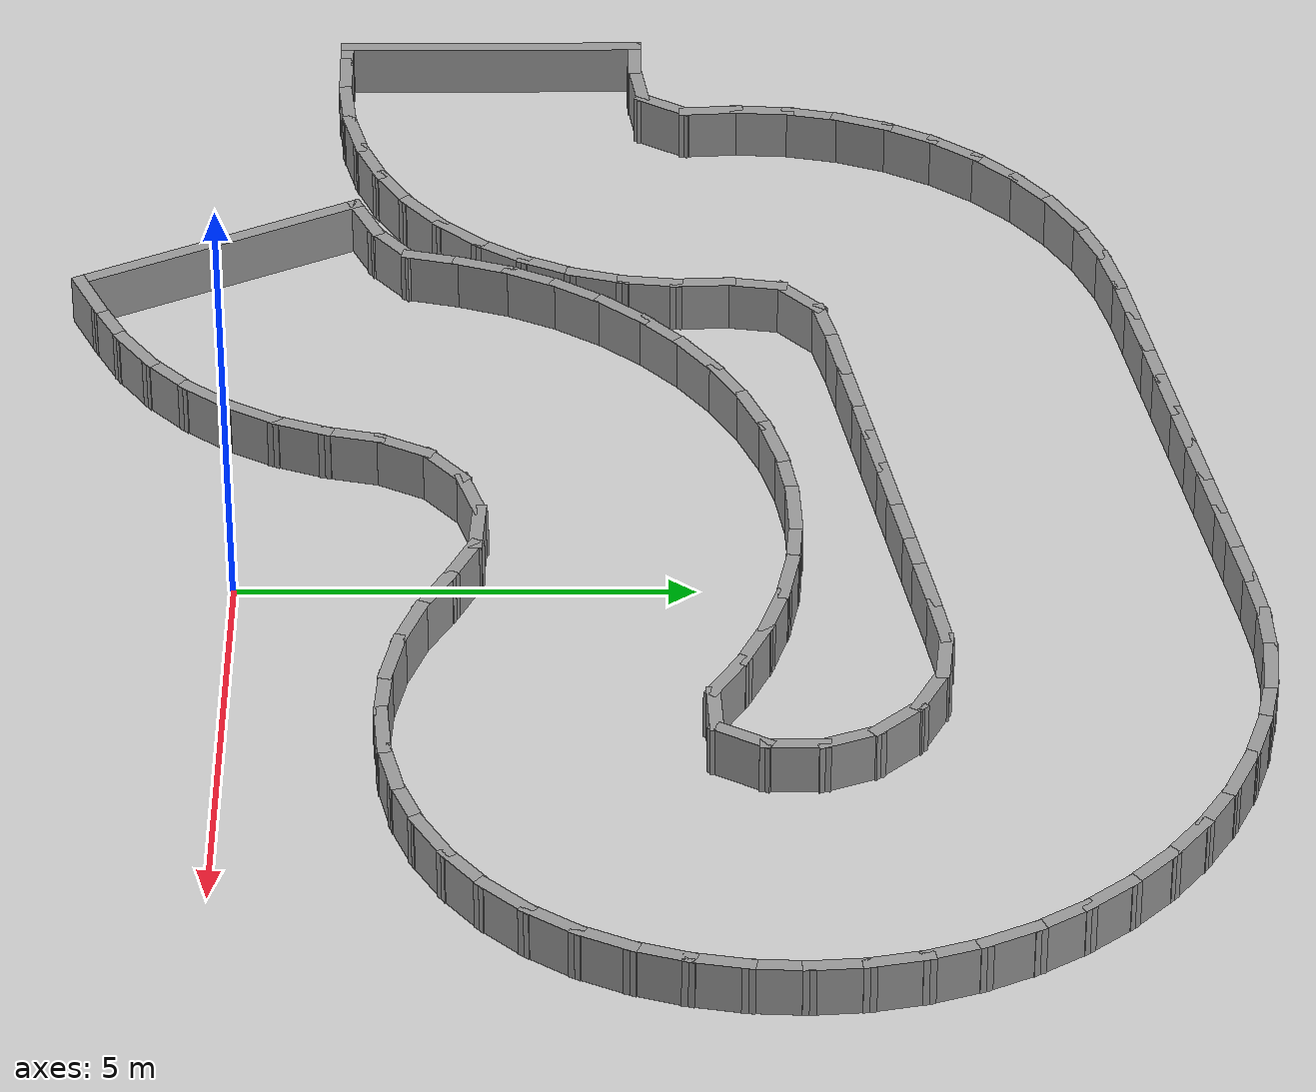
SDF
<?xml version="1.0" ?>
<sdf version='1.7'>
  <world name='default'>
    <plugin name='gazebo_ros_state' filename='libgazebo_ros_state.so'>
      <ros>
        <namespace>/</namespace>
      </ros>
      <update_rate>1000.0</update_rate>
    </plugin>

    <light name='sun' type='directional'>
      <cast_shadows>1</cast_shadows>
      <pose>0 0 10 0 -0 0</pose>
      <diffuse>0.8 0.8 0.8 1</diffuse>
      <specular>0.2 0.2 0.2 1</specular>
      <attenuation>
        <range>1000</range>
        <constant>0.9</constant>
        <linear>0.01</linear>
        <quadratic>0.001</quadratic>
      </attenuation>
      <direction>-0.5 0.1 -0.9</direction>
      <spot>
        <inner_angle>0</inner_angle>
        <outer_angle>0</outer_angle>
        <falloff>0</falloff>
      </spot>
    </light>
    <model name='ground_plane'>
      <static>1</static>
      <link name='link'>
        <collision name='collision'>
          <geometry>
            <plane>
              <normal>0 0 1</normal>
              <size>100 100</size>
            </plane>
          </geometry>
          <surface>
            <friction>
              <ode>
                <mu>100</mu>
                <mu2>50</mu2>
              </ode>
              <torsional>
                <ode/>
              </torsional>
            </friction>
            <contact>
              <ode/>
            </contact>
            <bounce/>
          </surface>
          <max_contacts>10</max_contacts>
        </collision>
        <visual name='visual'>
          <cast_shadows>0</cast_shadows>
          <geometry>
            <plane>
              <normal>0 0 1</normal>
              <size>100 100</size>
            </plane>
          </geometry>
          <material>
            <script>
              <uri>file://media/materials/scripts/gazebo.material</uri>
              <name>Gazebo/Grey</name>
            </script>
          </material>
        </visual>
        <self_collide>0</self_collide>
        <enable_wind>0</enable_wind>
        <kinematic>0</kinematic>
      </link>
    </model>
    <gravity>0 0 -9.8</gravity>
    <magnetic_field>6e-06 2.3e-05 -4.2e-05</magnetic_field>
    <atmosphere type='adiabatic'/>
    <physics type='ode'>
      <max_step_size>0.001</max_step_size>
      <real_time_factor>1</real_time_factor>
      <real_time_update_rate>1000</real_time_update_rate>
    </physics>
    <scene>
      <ambient>0.4 0.4 0.4 1</ambient>
      <background>0.7 0.7 0.7 1</background>
      <shadows>1</shadows>
    </scene>
    <audio>
      <device>default</device>
    </audio>
    <wind/>
    <spherical_coordinates>
      <surface_model>EARTH_WGS84</surface_model>
      <latitude_deg>0</latitude_deg>
      <longitude_deg>0</longitude_deg>
      <elevation>0</elevation>
      <heading_deg>0</heading_deg>
    </spherical_coordinates>
  <model name='rand_turn_07'>
    <pose>0 0 0 0 -0 0</pose>
    <link name='Wall_0'>
      <collision name='Wall_0_Collision'>
        <geometry><box><size>0.7500 0.1500 0.6000</size></box></geometry>
        <pose>0 0 0.3000 0 -0 0</pose>
      </collision>
      <visual name='Wall_0_Visual'>
        <pose>0 0 0.3000 0 -0 0</pose>
        <geometry><box><size>0.7500 0.1500 0.6000</size></box></geometry>
        <material>
          <script>
            <uri>file://media/materials/scripts/gazebo.material</uri>
            <name>Gazebo/Grey</name>
          </script>
          <ambient>1 1 1 1</ambient>
        </material>
      </visual>
      <pose>-6.0920 1.2048 0 0 -0 0.45567</pose>
    </link>
    <link name='Wall_1'>
      <collision name='Wall_1_Collision'>
        <geometry><box><size>0.7337 0.1500 0.6000</size></box></geometry>
        <pose>0 0 0.3000 0 -0 0</pose>
      </collision>
      <visual name='Wall_1_Visual'>
        <pose>0 0 0.3000 0 -0 0</pose>
        <geometry><box><size>0.7337 0.1500 0.6000</size></box></geometry>
        <material>
          <script>
            <uri>file://media/materials/scripts/gazebo.material</uri>
            <name>Gazebo/Grey</name>
          </script>
          <ambient>1 1 1 1</ambient>
        </material>
      </visual>
      <pose>-5.6029 1.5290 0 0 -0 0.71843</pose>
    </link>
    <link name='Wall_2'>
      <collision name='Wall_2_Collision'>
        <geometry><box><size>0.7490 0.1500 0.6000</size></box></geometry>
        <pose>0 0 0.3000 0 -0 0</pose>
      </collision>
      <visual name='Wall_2_Visual'>
        <pose>0 0 0.3000 0 -0 0</pose>
        <geometry><box><size>0.7490 0.1500 0.6000</size></box></geometry>
        <material>
          <script>
            <uri>file://media/materials/scripts/gazebo.material</uri>
            <name>Gazebo/Grey</name>
          </script>
          <ambient>1 1 1 1</ambient>
        </material>
      </visual>
      <pose>-5.3179 2.0134 0 0 -0 1.35128</pose>
    </link>
    <link name='Wall_3'>
      <collision name='Wall_3_Collision'>
        <geometry><box><size>0.7496 0.1500 0.6000</size></box></geometry>
        <pose>0 0 0.3000 0 -0 0</pose>
      </collision>
      <visual name='Wall_3_Visual'>
        <pose>0 0 0.3000 0 -0 0</pose>
        <geometry><box><size>0.7496 0.1500 0.6000</size></box></geometry>
        <material>
          <script>
            <uri>file://media/materials/scripts/gazebo.material</uri>
            <name>Gazebo/Grey</name>
          </script>
          <ambient>1 1 1 1</ambient>
        </material>
      </visual>
      <pose>-5.1639 2.5920 0 0 -0 1.26996</pose>
    </link>
    <link name='Wall_4'>
      <collision name='Wall_4_Collision'>
        <geometry><box><size>0.7496 0.1500 0.6000</size></box></geometry>
        <pose>0 0 0.3000 0 -0 0</pose>
      </collision>
      <visual name='Wall_4_Visual'>
        <pose>0 0 0.3000 0 -0 0</pose>
        <geometry><box><size>0.7496 0.1500 0.6000</size></box></geometry>
        <material>
          <script>
            <uri>file://media/materials/scripts/gazebo.material</uri>
            <name>Gazebo/Grey</name>
          </script>
          <ambient>1 1 1 1</ambient>
        </material>
      </visual>
      <pose>-4.9521 3.1518 0 0 -0 1.14847</pose>
    </link>
    <link name='Wall_5'>
      <collision name='Wall_5_Collision'>
        <geometry><box><size>0.7496 0.1500 0.6000</size></box></geometry>
        <pose>0 0 0.3000 0 -0 0</pose>
      </collision>
      <visual name='Wall_5_Visual'>
        <pose>0 0 0.3000 0 -0 0</pose>
        <geometry><box><size>0.7496 0.1500 0.6000</size></box></geometry>
        <material>
          <script>
            <uri>file://media/materials/scripts/gazebo.material</uri>
            <name>Gazebo/Grey</name>
          </script>
          <ambient>1 1 1 1</ambient>
        </material>
      </visual>
      <pose>-4.6741 3.6818 0 0 -0 1.02698</pose>
    </link>
    <link name='Wall_6'>
      <collision name='Wall_6_Collision'>
        <geometry><box><size>0.7496 0.1500 0.6000</size></box></geometry>
        <pose>0 0 0.3000 0 -0 0</pose>
      </collision>
      <visual name='Wall_6_Visual'>
        <pose>0 0 0.3000 0 -0 0</pose>
        <geometry><box><size>0.7496 0.1500 0.6000</size></box></geometry>
        <material>
          <script>
            <uri>file://media/materials/scripts/gazebo.material</uri>
            <name>Gazebo/Grey</name>
          </script>
          <ambient>1 1 1 1</ambient>
        </material>
      </visual>
      <pose>-4.3339 4.1742 0 0 -0 0.90548</pose>
    </link>
    <link name='Wall_7'>
      <collision name='Wall_7_Collision'>
        <geometry><box><size>0.7496 0.1500 0.6000</size></box></geometry>
        <pose>0 0 0.3000 0 -0 0</pose>
      </collision>
      <visual name='Wall_7_Visual'>
        <pose>0 0 0.3000 0 -0 0</pose>
        <geometry><box><size>0.7496 0.1500 0.6000</size></box></geometry>
        <material>
          <script>
            <uri>file://media/materials/scripts/gazebo.material</uri>
            <name>Gazebo/Grey</name>
          </script>
          <ambient>1 1 1 1</ambient>
        </material>
      </visual>
      <pose>-3.9366 4.6218 0 0 -0 0.78399</pose>
    </link>
    <link name='Wall_8'>
      <collision name='Wall_8_Collision'>
        <geometry><box><size>0.7496 0.1500 0.6000</size></box></geometry>
        <pose>0 0 0.3000 0 -0 0</pose>
      </collision>
      <visual name='Wall_8_Visual'>
        <pose>0 0 0.3000 0 -0 0</pose>
        <geometry><box><size>0.7496 0.1500 0.6000</size></box></geometry>
        <material>
          <script>
            <uri>file://media/materials/scripts/gazebo.material</uri>
            <name>Gazebo/Grey</name>
          </script>
          <ambient>1 1 1 1</ambient>
        </material>
      </visual>
      <pose>-3.4879 5.0179 0 0 -0 0.66250</pose>
    </link>
    <link name='Wall_9'>
      <collision name='Wall_9_Collision'>
        <geometry><box><size>0.7496 0.1500 0.6000</size></box></geometry>
        <pose>0 0 0.3000 0 -0 0</pose>
      </collision>
      <visual name='Wall_9_Visual'>
        <pose>0 0 0.3000 0 -0 0</pose>
        <geometry><box><size>0.7496 0.1500 0.6000</size></box></geometry>
        <material>
          <script>
            <uri>file://media/materials/scripts/gazebo.material</uri>
            <name>Gazebo/Grey</name>
          </script>
          <ambient>1 1 1 1</ambient>
        </material>
      </visual>
      <pose>-2.9946 5.3567 0 0 -0 0.54100</pose>
    </link>
    <link name='Wall_10'>
      <collision name='Wall_10_Collision'>
        <geometry><box><size>0.7496 0.1500 0.6000</size></box></geometry>
        <pose>0 0 0.3000 0 -0 0</pose>
      </collision>
      <visual name='Wall_10_Visual'>
        <pose>0 0 0.3000 0 -0 0</pose>
        <geometry><box><size>0.7496 0.1500 0.6000</size></box></geometry>
        <material>
          <script>
            <uri>file://media/materials/scripts/gazebo.material</uri>
            <name>Gazebo/Grey</name>
          </script>
          <ambient>1 1 1 1</ambient>
        </material>
      </visual>
      <pose>-2.4638 5.6332 0 0 -0 0.41951</pose>
    </link>
    <link name='Wall_11'>
      <collision name='Wall_11_Collision'>
        <geometry><box><size>0.7496 0.1500 0.6000</size></box></geometry>
        <pose>0 0 0.3000 0 -0 0</pose>
      </collision>
      <visual name='Wall_11_Visual'>
        <pose>0 0 0.3000 0 -0 0</pose>
        <geometry><box><size>0.7496 0.1500 0.6000</size></box></geometry>
        <material>
          <script>
            <uri>file://media/materials/scripts/gazebo.material</uri>
            <name>Gazebo/Grey</name>
          </script>
          <ambient>1 1 1 1</ambient>
        </material>
      </visual>
      <pose>-1.9034 5.8433 0 0 -0 0.29802</pose>
    </link>
    <link name='Wall_12'>
      <collision name='Wall_12_Collision'>
        <geometry><box><size>0.7496 0.1500 0.6000</size></box></geometry>
        <pose>0 0 0.3000 0 -0 0</pose>
      </collision>
      <visual name='Wall_12_Visual'>
        <pose>0 0 0.3000 0 -0 0</pose>
        <geometry><box><size>0.7496 0.1500 0.6000</size></box></geometry>
        <material>
          <script>
            <uri>file://media/materials/scripts/gazebo.material</uri>
            <name>Gazebo/Grey</name>
          </script>
          <ambient>1 1 1 1</ambient>
        </material>
      </visual>
      <pose>-1.3217 5.9840 0 0 -0 0.17653</pose>
    </link>
    <link name='Wall_13'>
      <collision name='Wall_13_Collision'>
        <geometry><box><size>0.7496 0.1500 0.6000</size></box></geometry>
        <pose>0 0 0.3000 0 -0 0</pose>
      </collision>
      <visual name='Wall_13_Visual'>
        <pose>0 0 0.3000 0 -0 0</pose>
        <geometry><box><size>0.7496 0.1500 0.6000</size></box></geometry>
        <material>
          <script>
            <uri>file://media/materials/scripts/gazebo.material</uri>
            <name>Gazebo/Grey</name>
          </script>
          <ambient>1 1 1 1</ambient>
        </material>
      </visual>
      <pose>-0.7272 6.0531 0 0 -0 0.05503</pose>
    </link>
    <link name='Wall_14'>
      <collision name='Wall_14_Collision'>
        <geometry><box><size>0.7496 0.1500 0.6000</size></box></geometry>
        <pose>0 0 0.3000 0 -0 0</pose>
      </collision>
      <visual name='Wall_14_Visual'>
        <pose>0 0 0.3000 0 -0 0</pose>
        <geometry><box><size>0.7496 0.1500 0.6000</size></box></geometry>
        <material>
          <script>
            <uri>file://media/materials/scripts/gazebo.material</uri>
            <name>Gazebo/Grey</name>
          </script>
          <ambient>1 1 1 1</ambient>
        </material>
      </visual>
      <pose>-0.1287 6.0497 0 0 -0 -0.06646</pose>
    </link>
    <link name='Wall_15'>
      <collision name='Wall_15_Collision'>
        <geometry><box><size>0.7496 0.1500 0.6000</size></box></geometry>
        <pose>0 0 0.3000 0 -0 0</pose>
      </collision>
      <visual name='Wall_15_Visual'>
        <pose>0 0 0.3000 0 -0 0</pose>
        <geometry><box><size>0.7496 0.1500 0.6000</size></box></geometry>
        <material>
          <script>
            <uri>file://media/materials/scripts/gazebo.material</uri>
            <name>Gazebo/Grey</name>
          </script>
          <ambient>1 1 1 1</ambient>
        </material>
      </visual>
      <pose>0.4650 5.9738 0 0 -0 -0.18795</pose>
    </link>
    <link name='Wall_16'>
      <collision name='Wall_16_Collision'>
        <geometry><box><size>0.7496 0.1500 0.6000</size></box></geometry>
        <pose>0 0 0.3000 0 -0 0</pose>
      </collision>
      <visual name='Wall_16_Visual'>
        <pose>0 0 0.3000 0 -0 0</pose>
        <geometry><box><size>0.7496 0.1500 0.6000</size></box></geometry>
        <material>
          <script>
            <uri>file://media/materials/scripts/gazebo.material</uri>
            <name>Gazebo/Grey</name>
          </script>
          <ambient>1 1 1 1</ambient>
        </material>
      </visual>
      <pose>1.0451 5.8263 0 0 -0 -0.30997</pose>
    </link>
    <link name='Wall_17'>
      <collision name='Wall_17_Collision'>
        <geometry><box><size>0.7496 0.1500 0.6000</size></box></geometry>
        <pose>0 0 0.3000 0 -0 0</pose>
      </collision>
      <visual name='Wall_17_Visual'>
        <pose>0 0 0.3000 0 -0 0</pose>
        <geometry><box><size>0.7496 0.1500 0.6000</size></box></geometry>
        <material>
          <script>
            <uri>file://media/materials/scripts/gazebo.material</uri>
            <name>Gazebo/Grey</name>
          </script>
          <ambient>1 1 1 1</ambient>
        </material>
      </visual>
      <pose>1.6029 5.6095 0 0 -0 -0.43148</pose>
    </link>
    <link name='Wall_18'>
      <collision name='Wall_18_Collision'>
        <geometry><box><size>0.7497 0.1500 0.6000</size></box></geometry>
        <pose>0 0 0.3000 0 -0 0</pose>
      </collision>
      <visual name='Wall_18_Visual'>
        <pose>0 0 0.3000 0 -0 0</pose>
        <geometry><box><size>0.7497 0.1500 0.6000</size></box></geometry>
        <material>
          <script>
            <uri>file://media/materials/scripts/gazebo.material</uri>
            <name>Gazebo/Grey</name>
          </script>
          <ambient>1 1 1 1</ambient>
        </material>
      </visual>
      <pose>2.1314 5.3282 0 0 -0 -0.54661</pose>
    </link>
    <link name='Wall_19'>
      <collision name='Wall_19_Collision'>
        <geometry><box><size>0.7203 0.1500 0.6000</size></box></geometry>
        <pose>0 0 0.3000 0 -0 0</pose>
      </collision>
      <visual name='Wall_19_Visual'>
        <pose>0 0 0.3000 0 -0 0</pose>
        <geometry><box><size>0.7203 0.1500 0.6000</size></box></geometry>
        <material>
          <script>
            <uri>file://media/materials/scripts/gazebo.material</uri>
            <name>Gazebo/Grey</name>
          </script>
          <ambient>1 1 1 1</ambient>
        </material>
      </visual>
      <pose>2.6722 5.1901 0 0 -0 0.06224</pose>
    </link>
    <link name='Wall_20'>
      <collision name='Wall_20_Collision'>
        <geometry><box><size>0.7338 0.1500 0.6000</size></box></geometry>
        <pose>0 0 0.3000 0 -0 0</pose>
      </collision>
      <visual name='Wall_20_Visual'>
        <pose>0 0 0.3000 0 -0 0</pose>
        <geometry><box><size>0.7338 0.1500 0.6000</size></box></geometry>
        <material>
          <script>
            <uri>file://media/materials/scripts/gazebo.material</uri>
            <name>Gazebo/Grey</name>
          </script>
          <ambient>1 1 1 1</ambient>
        </material>
      </visual>
      <pose>3.0927 5.4662 0 0 -0 1.08660</pose>
    </link>
    <link name='Wall_21'>
      <collision name='Wall_21_Collision'>
        <geometry><box><size>0.7465 0.1500 0.6000</size></box></geometry>
        <pose>0 0 0.3000 0 -0 0</pose>
      </collision>
      <visual name='Wall_21_Visual'>
        <pose>0 0 0.3000 0 -0 0</pose>
        <geometry><box><size>0.7465 0.1500 0.6000</size></box></geometry>
        <material>
          <script>
            <uri>file://media/materials/scripts/gazebo.material</uri>
            <name>Gazebo/Grey</name>
          </script>
          <ambient>1 1 1 1</ambient>
        </material>
      </visual>
      <pose>3.2300 6.0228 0 0 -0 1.56584</pose>
    </link>
    <link name='Wall_22'>
      <collision name='Wall_22_Collision'>
        <geometry><box><size>0.7465 0.1500 0.6000</size></box></geometry>
        <pose>0 0 0.3000 0 -0 0</pose>
      </collision>
      <visual name='Wall_22_Visual'>
        <pose>0 0 0.3000 0 -0 0</pose>
        <geometry><box><size>0.7465 0.1500 0.6000</size></box></geometry>
        <material>
          <script>
            <uri>file://media/materials/scripts/gazebo.material</uri>
            <name>Gazebo/Grey</name>
          </script>
          <ambient>1 1 1 1</ambient>
        </material>
      </visual>
      <pose>3.1246 6.5995 0 0 -0 1.93747</pose>
    </link>
    <link name='Wall_23'>
      <collision name='Wall_23_Collision'>
        <geometry><box><size>0.7465 0.1500 0.6000</size></box></geometry>
        <pose>0 0 0.3000 0 -0 0</pose>
      </collision>
      <visual name='Wall_23_Visual'>
        <pose>0 0 0.3000 0 -0 0</pose>
        <geometry><box><size>0.7465 0.1500 0.6000</size></box></geometry>
        <material>
          <script>
            <uri>file://media/materials/scripts/gazebo.material</uri>
            <name>Gazebo/Grey</name>
          </script>
          <ambient>1 1 1 1</ambient>
        </material>
      </visual>
      <pose>2.8170 7.0987 0 0 -0 2.30850</pose>
    </link>
    <link name='Wall_24'>
      <collision name='Wall_24_Collision'>
        <geometry><box><size>0.7465 0.1500 0.6000</size></box></geometry>
        <pose>0 0 0.3000 0 -0 0</pose>
      </collision>
      <visual name='Wall_24_Visual'>
        <pose>0 0 0.3000 0 -0 0</pose>
        <geometry><box><size>0.7465 0.1500 0.6000</size></box></geometry>
        <material>
          <script>
            <uri>file://media/materials/scripts/gazebo.material</uri>
            <name>Gazebo/Grey</name>
          </script>
          <ambient>1 1 1 1</ambient>
        </material>
      </visual>
      <pose>2.3494 7.4523 0 0 -0 2.67965</pose>
    </link>
    <link name='Wall_25'>
      <collision name='Wall_25_Collision'>
        <geometry><box><size>0.7465 0.1500 0.6000</size></box></geometry>
        <pose>0 0 0.3000 0 -0 0</pose>
      </collision>
      <visual name='Wall_25_Visual'>
        <pose>0 0 0.3000 0 -0 0</pose>
        <geometry><box><size>0.7465 0.1500 0.6000</size></box></geometry>
        <material>
          <script>
            <uri>file://media/materials/scripts/gazebo.material</uri>
            <name>Gazebo/Grey</name>
          </script>
          <ambient>1 1 1 1</ambient>
        </material>
      </visual>
      <pose>1.7853 7.6121 0 0 -0 3.05135</pose>
    </link>
    <link name='Wall_26'>
      <collision name='Wall_26_Collision'>
        <geometry><box><size>0.7497 0.1500 0.6000</size></box></geometry>
        <pose>0 0 0.3000 0 -0 0</pose>
      </collision>
      <visual name='Wall_26_Visual'>
        <pose>0 0 0.3000 0 -0 0</pose>
        <geometry><box><size>0.7497 0.1500 0.6000</size></box></geometry>
        <material>
          <script>
            <uri>file://media/materials/scripts/gazebo.material</uri>
            <name>Gazebo/Grey</name>
          </script>
          <ambient>1 1 1 1</ambient>
        </material>
      </visual>
      <pose>1.1940 7.5816 0 0 -0 -2.94908</pose>
    </link>
    <link name='Wall_27'>
      <collision name='Wall_27_Collision'>
        <geometry><box><size>0.7500 0.1500 0.6000</size></box></geometry>
        <pose>0 0 0.3000 0 -0 0</pose>
      </collision>
      <visual name='Wall_27_Visual'>
        <pose>0 0 0.3000 0 -0 0</pose>
        <geometry><box><size>0.7500 0.1500 0.6000</size></box></geometry>
        <material>
          <script>
            <uri>file://media/materials/scripts/gazebo.material</uri>
            <name>Gazebo/Grey</name>
          </script>
          <ambient>1 1 1 1</ambient>
        </material>
      </visual>
      <pose>0.6063 7.4615 0 0 -0 -2.93095</pose>
    </link>
    <link name='Wall_28'>
      <collision name='Wall_28_Collision'>
        <geometry><box><size>0.7500 0.1500 0.6000</size></box></geometry>
        <pose>0 0 0.3000 0 -0 0</pose>
      </collision>
      <visual name='Wall_28_Visual'>
        <pose>0 0 0.3000 0 -0 0</pose>
        <geometry><box><size>0.7500 0.1500 0.6000</size></box></geometry>
        <material>
          <script>
            <uri>file://media/materials/scripts/gazebo.material</uri>
            <name>Gazebo/Grey</name>
          </script>
          <ambient>1 1 1 1</ambient>
        </material>
      </visual>
      <pose>0.0196 7.3361 0 0 -0 -2.93095</pose>
    </link>
    <link name='Wall_29'>
      <collision name='Wall_29_Collision'>
        <geometry><box><size>0.7500 0.1500 0.6000</size></box></geometry>
        <pose>0 0 0.3000 0 -0 0</pose>
      </collision>
      <visual name='Wall_29_Visual'>
        <pose>0 0 0.3000 0 -0 0</pose>
        <geometry><box><size>0.7500 0.1500 0.6000</size></box></geometry>
        <material>
          <script>
            <uri>file://media/materials/scripts/gazebo.material</uri>
            <name>Gazebo/Grey</name>
          </script>
          <ambient>1 1 1 1</ambient>
        </material>
      </visual>
      <pose>-0.5672 7.2106 0 0 -0 -2.93095</pose>
    </link>
    <link name='Wall_30'>
      <collision name='Wall_30_Collision'>
        <geometry><box><size>0.7500 0.1500 0.6000</size></box></geometry>
        <pose>0 0 0.3000 0 -0 0</pose>
      </collision>
      <visual name='Wall_30_Visual'>
        <pose>0 0 0.3000 0 -0 0</pose>
        <geometry><box><size>0.7500 0.1500 0.6000</size></box></geometry>
        <material>
          <script>
            <uri>file://media/materials/scripts/gazebo.material</uri>
            <name>Gazebo/Grey</name>
          </script>
          <ambient>1 1 1 1</ambient>
        </material>
      </visual>
      <pose>-1.1539 7.0852 0 0 -0 -2.93095</pose>
    </link>
    <link name='Wall_31'>
      <collision name='Wall_31_Collision'>
        <geometry><box><size>0.7500 0.1500 0.6000</size></box></geometry>
        <pose>0 0 0.3000 0 -0 0</pose>
      </collision>
      <visual name='Wall_31_Visual'>
        <pose>0 0 0.3000 0 -0 0</pose>
        <geometry><box><size>0.7500 0.1500 0.6000</size></box></geometry>
        <material>
          <script>
            <uri>file://media/materials/scripts/gazebo.material</uri>
            <name>Gazebo/Grey</name>
          </script>
          <ambient>1 1 1 1</ambient>
        </material>
      </visual>
      <pose>-1.7406 6.9597 0 0 -0 -2.93095</pose>
    </link>
    <link name='Wall_32'>
      <collision name='Wall_32_Collision'>
        <geometry><box><size>0.7500 0.1500 0.6000</size></box></geometry>
        <pose>0 0 0.3000 0 -0 0</pose>
      </collision>
      <visual name='Wall_32_Visual'>
        <pose>0 0 0.3000 0 -0 0</pose>
        <geometry><box><size>0.7500 0.1500 0.6000</size></box></geometry>
        <material>
          <script>
            <uri>file://media/materials/scripts/gazebo.material</uri>
            <name>Gazebo/Grey</name>
          </script>
          <ambient>1 1 1 1</ambient>
        </material>
      </visual>
      <pose>-2.3274 6.8343 0 0 -0 -2.93095</pose>
    </link>
    <link name='Wall_33'>
      <collision name='Wall_33_Collision'>
        <geometry><box><size>0.7500 0.1500 0.6000</size></box></geometry>
        <pose>0 0 0.3000 0 -0 0</pose>
      </collision>
      <visual name='Wall_33_Visual'>
        <pose>0 0 0.3000 0 -0 0</pose>
        <geometry><box><size>0.7500 0.1500 0.6000</size></box></geometry>
        <material>
          <script>
            <uri>file://media/materials/scripts/gazebo.material</uri>
            <name>Gazebo/Grey</name>
          </script>
          <ambient>1 1 1 1</ambient>
        </material>
      </visual>
      <pose>-2.9141 6.7088 0 0 -0 -2.93095</pose>
    </link>
    <link name='Wall_34'>
      <collision name='Wall_34_Collision'>
        <geometry><box><size>0.7500 0.1500 0.6000</size></box></geometry>
        <pose>0 0 0.3000 0 -0 0</pose>
      </collision>
      <visual name='Wall_34_Visual'>
        <pose>0 0 0.3000 0 -0 0</pose>
        <geometry><box><size>0.7500 0.1500 0.6000</size></box></geometry>
        <material>
          <script>
            <uri>file://media/materials/scripts/gazebo.material</uri>
            <name>Gazebo/Grey</name>
          </script>
          <ambient>1 1 1 1</ambient>
        </material>
      </visual>
      <pose>-3.5009 6.5834 0 0 -0 -2.93095</pose>
    </link>
    <link name='Wall_35'>
      <collision name='Wall_35_Collision'>
        <geometry><box><size>0.7482 0.1500 0.6000</size></box></geometry>
        <pose>0 0 0.3000 0 -0 0</pose>
      </collision>
      <visual name='Wall_35_Visual'>
        <pose>0 0 0.3000 0 -0 0</pose>
        <geometry><box><size>0.7482 0.1500 0.6000</size></box></geometry>
        <material>
          <script>
            <uri>file://media/materials/scripts/gazebo.material</uri>
            <name>Gazebo/Grey</name>
          </script>
          <ambient>1 1 1 1</ambient>
        </material>
      </visual>
      <pose>-4.0833 6.4438 0 0 -0 -2.88164</pose>
    </link>
    <link name='Wall_36'>
      <collision name='Wall_36_Collision'>
        <geometry><box><size>0.7395 0.1500 0.6000</size></box></geometry>
        <pose>0 0 0.3000 0 -0 0</pose>
      </collision>
      <visual name='Wall_36_Visual'>
        <pose>0 0 0.3000 0 -0 0</pose>
        <geometry><box><size>0.7395 0.1500 0.6000</size></box></geometry>
        <material>
          <script>
            <uri>file://media/materials/scripts/gazebo.material</uri>
            <name>Gazebo/Grey</name>
          </script>
          <ambient>1 1 1 1</ambient>
        </material>
      </visual>
      <pose>-4.5806 6.1582 0 0 -0 -2.35509</pose>
    </link>
    <link name='Wall_37'>
      <collision name='Wall_37_Collision'>
        <geometry><box><size>0.7401 0.1500 0.6000</size></box></geometry>
        <pose>0 0 0.3000 0 -0 0</pose>
      </collision>
      <visual name='Wall_37_Visual'>
        <pose>0 0 0.3000 0 -0 0</pose>
        <geometry><box><size>0.7401 0.1500 0.6000</size></box></geometry>
        <material>
          <script>
            <uri>file://media/materials/scripts/gazebo.material</uri>
            <name>Gazebo/Grey</name>
          </script>
          <ambient>1 1 1 1</ambient>
        </material>
      </visual>
      <pose>-4.8301 5.6574 0 0 -0 -1.71134</pose>
    </link>
    <link name='Wall_38'>
      <collision name='Wall_38_Collision'>
        <geometry><box><size>0.7494 0.1500 0.6000</size></box></geometry>
        <pose>0 0 0.3000 0 -0 0</pose>
      </collision>
      <visual name='Wall_38_Visual'>
        <pose>0 0 0.3000 0 -0 0</pose>
        <geometry><box><size>0.7494 0.1500 0.6000</size></box></geometry>
        <material>
          <script>
            <uri>file://media/materials/scripts/gazebo.material</uri>
            <name>Gazebo/Grey</name>
          </script>
          <ambient>1 1 1 1</ambient>
        </material>
      </visual>
      <pose>-4.8572 5.0659 0 0 -0 -1.52324</pose>
    </link>
    <link name='Wall_39'>
      <collision name='Wall_39_Collision'>
        <geometry><box><size>0.7494 0.1500 0.6000</size></box></geometry>
        <pose>0 0 0.3000 0 -0 0</pose>
      </collision>
      <visual name='Wall_39_Visual'>
        <pose>0 0 0.3000 0 -0 0</pose>
        <geometry><box><size>0.7494 0.1500 0.6000</size></box></geometry>
        <material>
          <script>
            <uri>file://media/materials/scripts/gazebo.material</uri>
            <name>Gazebo/Grey</name>
          </script>
          <ambient>1 1 1 1</ambient>
        </material>
      </visual>
      <pose>-4.8741 4.4684 0 0 -0 -1.67497</pose>
    </link>
    <link name='Wall_40'>
      <collision name='Wall_40_Collision'>
        <geometry><box><size>0.7494 0.1500 0.6000</size></box></geometry>
        <pose>0 0 0.3000 0 -0 0</pose>
      </collision>
      <visual name='Wall_40_Visual'>
        <pose>0 0 0.3000 0 -0 0</pose>
        <geometry><box><size>0.7494 0.1500 0.6000</size></box></geometry>
        <material>
          <script>
            <uri>file://media/materials/scripts/gazebo.material</uri>
            <name>Gazebo/Grey</name>
          </script>
          <ambient>1 1 1 1</ambient>
        </material>
      </visual>
      <pose>-4.9796 3.8800 0 0 -0 -1.82162</pose>
    </link>
    <link name='Wall_41'>
      <collision name='Wall_41_Collision'>
        <geometry><box><size>0.7494 0.1500 0.6000</size></box></geometry>
        <pose>0 0 0.3000 0 -0 0</pose>
      </collision>
      <visual name='Wall_41_Visual'>
        <pose>0 0 0.3000 0 -0 0</pose>
        <geometry><box><size>0.7494 0.1500 0.6000</size></box></geometry>
        <material>
          <script>
            <uri>file://media/materials/scripts/gazebo.material</uri>
            <name>Gazebo/Grey</name>
          </script>
          <ambient>1 1 1 1</ambient>
        </material>
      </visual>
      <pose>-5.1714 3.3139 0 0 -0 -1.97326</pose>
    </link>
    <link name='Wall_42'>
      <collision name='Wall_42_Collision'>
        <geometry><box><size>0.7494 0.1500 0.6000</size></box></geometry>
        <pose>0 0 0.3000 0 -0 0</pose>
      </collision>
      <visual name='Wall_42_Visual'>
        <pose>0 0 0.3000 0 -0 0</pose>
        <geometry><box><size>0.7494 0.1500 0.6000</size></box></geometry>
        <material>
          <script>
            <uri>file://media/materials/scripts/gazebo.material</uri>
            <name>Gazebo/Grey</name>
          </script>
          <ambient>1 1 1 1</ambient>
        </material>
      </visual>
      <pose>-5.4454 2.7827 0 0 -0 -2.12064</pose>
    </link>
    <link name='Wall_43'>
      <collision name='Wall_43_Collision'>
        <geometry><box><size>0.7494 0.1500 0.6000</size></box></geometry>
        <pose>0 0 0.3000 0 -0 0</pose>
      </collision>
      <visual name='Wall_43_Visual'>
        <pose>0 0 0.3000 0 -0 0</pose>
        <geometry><box><size>0.7494 0.1500 0.6000</size></box></geometry>
        <material>
          <script>
            <uri>file://media/materials/scripts/gazebo.material</uri>
            <name>Gazebo/Grey</name>
          </script>
          <ambient>1 1 1 1</ambient>
        </material>
      </visual>
      <pose>-5.7952 2.2980 0 0 -0 -2.27124</pose>
    </link>
    <link name='Wall_44'>
      <collision name='Wall_44_Collision'>
        <geometry><box><size>0.7494 0.1500 0.6000</size></box></geometry>
        <pose>0 0 0.3000 0 -0 0</pose>
      </collision>
      <visual name='Wall_44_Visual'>
        <pose>0 0 0.3000 0 -0 0</pose>
        <geometry><box><size>0.7494 0.1500 0.6000</size></box></geometry>
        <material>
          <script>
            <uri>file://media/materials/scripts/gazebo.material</uri>
            <name>Gazebo/Grey</name>
          </script>
          <ambient>1 1 1 1</ambient>
        </material>
      </visual>
      <pose>-6.2133 1.8708 0 0 -0 -2.41966</pose>
    </link>
    <link name='Wall_45'>
      <collision name='Wall_45_Collision'>
        <geometry><box><size>0.7494 0.1500 0.6000</size></box></geometry>
        <pose>0 0 0.3000 0 -0 0</pose>
      </collision>
      <visual name='Wall_45_Visual'>
        <pose>0 0 0.3000 0 -0 0</pose>
        <geometry><box><size>0.7494 0.1500 0.6000</size></box></geometry>
        <material>
          <script>
            <uri>file://media/materials/scripts/gazebo.material</uri>
            <name>Gazebo/Grey</name>
          </script>
          <ambient>1 1 1 1</ambient>
        </material>
      </visual>
      <pose>-6.6901 1.5105 0 0 -0 -2.56922</pose>
    </link>
    <link name='Wall_46'>
      <collision name='Wall_46_Collision'>
        <geometry><box><size>0.7494 0.1500 0.6000</size></box></geometry>
        <pose>0 0 0.3000 0 -0 0</pose>
      </collision>
      <visual name='Wall_46_Visual'>
        <pose>0 0 0.3000 0 -0 0</pose>
        <geometry><box><size>0.7494 0.1500 0.6000</size></box></geometry>
        <material>
          <script>
            <uri>file://media/materials/scripts/gazebo.material</uri>
            <name>Gazebo/Grey</name>
          </script>
          <ambient>1 1 1 1</ambient>
        </material>
      </visual>
      <pose>-7.2154 1.2251 0 0 -0 -2.71868</pose>
    </link>
    <link name='Wall_47'>
      <collision name='Wall_47_Collision'>
        <geometry><box><size>0.7494 0.1500 0.6000</size></box></geometry>
        <pose>0 0 0.3000 0 -0 0</pose>
      </collision>
      <visual name='Wall_47_Visual'>
        <pose>0 0 0.3000 0 -0 0</pose>
        <geometry><box><size>0.7494 0.1500 0.6000</size></box></geometry>
        <material>
          <script>
            <uri>file://media/materials/scripts/gazebo.material</uri>
            <name>Gazebo/Grey</name>
          </script>
          <ambient>1 1 1 1</ambient>
        </material>
      </visual>
      <pose>-7.7771 1.0209 0 0 -0 -2.86720</pose>
    </link>
    <link name='Wall_48'>
      <collision name='Wall_48_Collision'>
        <geometry><box><size>0.7494 0.1500 0.6000</size></box></geometry>
        <pose>0 0 0.3000 0 -0 0</pose>
      </collision>
      <visual name='Wall_48_Visual'>
        <pose>0 0 0.3000 0 -0 0</pose>
        <geometry><box><size>0.7494 0.1500 0.6000</size></box></geometry>
        <material>
          <script>
            <uri>file://media/materials/scripts/gazebo.material</uri>
            <name>Gazebo/Grey</name>
          </script>
          <ambient>1 1 1 1</ambient>
        </material>
      </visual>
      <pose>-8.3630 0.9027 0 0 -0 -3.01770</pose>
    </link>
    <link name='Wall_49'>
      <collision name='Wall_49_Collision'>
        <geometry><box><size>0.7499 0.1500 0.6000</size></box></geometry>
        <pose>0 0 0.3000 0 -0 0</pose>
      </collision>
      <visual name='Wall_49_Visual'>
        <pose>0 0 0.3000 0 -0 0</pose>
        <geometry><box><size>0.7499 0.1500 0.6000</size></box></geometry>
        <material>
          <script>
            <uri>file://media/materials/scripts/gazebo.material</uri>
            <name>Gazebo/Grey</name>
          </script>
          <ambient>1 1 1 1</ambient>
        </material>
      </visual>
      <pose>-8.9603 0.8606 0 0 -0 -3.12460</pose>
    </link>
    <link name='Wall_50'>
      <collision name='Wall_50_Collision'>
        <geometry><box><size>0.4548 0.1500 0.6000</size></box></geometry>
        <pose>0 0 0.3000 0 -0 0</pose>
      </collision>
      <visual name='Wall_50_Visual'>
        <pose>0 0 0.3000 0 -0 0</pose>
        <geometry><box><size>0.4548 0.1500 0.6000</size></box></geometry>
        <material>
          <script>
            <uri>file://media/materials/scripts/gazebo.material</uri>
            <name>Gazebo/Grey</name>
          </script>
          <ambient>1 1 1 1</ambient>
        </material>
      </visual>
      <pose>-9.4127 0.8537 0 0 -0 -3.13016</pose>
    </link>
    <link name='Wall_51'>
      <collision name='Wall_51_Collision'>
        <geometry><box><size>0.7500 0.1500 0.6000</size></box></geometry>
        <pose>0 0 0.3000 0 -0 0</pose>
      </collision>
      <visual name='Wall_51_Visual'>
        <pose>0 0 0.3000 0 -0 0</pose>
        <geometry><box><size>0.7500 0.1500 0.6000</size></box></geometry>
        <material>
          <script>
            <uri>file://media/materials/scripts/gazebo.material</uri>
            <name>Gazebo/Grey</name>
          </script>
          <ambient>1 1 1 1</ambient>
        </material>
      </visual>
      <pose>-4.5930 -1.8538 0 0 -0 0.45567</pose>
    </link>
    <link name='Wall_52'>
      <collision name='Wall_52_Collision'>
        <geometry><box><size>0.7496 0.1500 0.6000</size></box></geometry>
        <pose>0 0 0.3000 0 -0 0</pose>
      </collision>
      <visual name='Wall_52_Visual'>
        <pose>0 0 0.3000 0 -0 0</pose>
        <geometry><box><size>0.7496 0.1500 0.6000</size></box></geometry>
        <material>
          <script>
            <uri>file://media/materials/scripts/gazebo.material</uri>
            <name>Gazebo/Grey</name>
          </script>
          <ambient>1 1 1 1</ambient>
        </material>
      </visual>
      <pose>-4.0601 -1.5789 0 0 -0 0.49708</pose>
    </link>
    <link name='Wall_53'>
      <collision name='Wall_53_Collision'>
        <geometry><box><size>0.7494 0.1500 0.6000</size></box></geometry>
        <pose>0 0 0.3000 0 -0 0</pose>
      </collision>
      <visual name='Wall_53_Visual'>
        <pose>0 0 0.3000 0 -0 0</pose>
        <geometry><box><size>0.7494 0.1500 0.6000</size></box></geometry>
        <material>
          <script>
            <uri>file://media/materials/scripts/gazebo.material</uri>
            <name>Gazebo/Grey</name>
          </script>
          <ambient>1 1 1 1</ambient>
        </material>
      </visual>
      <pose>-3.5566 -1.2564 0 0 -0 0.64203</pose>
    </link>
    <link name='Wall_54'>
      <collision name='Wall_54_Collision'>
        <geometry><box><size>0.7494 0.1500 0.6000</size></box></geometry>
        <pose>0 0 0.3000 0 -0 0</pose>
      </collision>
      <visual name='Wall_54_Visual'>
        <pose>0 0 0.3000 0 -0 0</pose>
        <geometry><box><size>0.7494 0.1500 0.6000</size></box></geometry>
        <material>
          <script>
            <uri>file://media/materials/scripts/gazebo.material</uri>
            <name>Gazebo/Grey</name>
          </script>
          <ambient>1 1 1 1</ambient>
        </material>
      </visual>
      <pose>-3.1052 -0.8644 0 0 -0 0.78828</pose>
    </link>
    <link name='Wall_55'>
      <collision name='Wall_55_Collision'>
        <geometry><box><size>0.7494 0.1500 0.6000</size></box></geometry>
        <pose>0 0 0.3000 0 -0 0</pose>
      </collision>
      <visual name='Wall_55_Visual'>
        <pose>0 0 0.3000 0 -0 0</pose>
        <geometry><box><size>0.7494 0.1500 0.6000</size></box></geometry>
        <material>
          <script>
            <uri>file://media/materials/scripts/gazebo.material</uri>
            <name>Gazebo/Grey</name>
          </script>
          <ambient>1 1 1 1</ambient>
        </material>
      </visual>
      <pose>-2.7169 -0.4100 0 0 -0 0.93904</pose>
    </link>
    <link name='Wall_56'>
      <collision name='Wall_56_Collision'>
        <geometry><box><size>0.7494 0.1500 0.6000</size></box></geometry>
        <pose>0 0 0.3000 0 -0 0</pose>
      </collision>
      <visual name='Wall_56_Visual'>
        <pose>0 0 0.3000 0 -0 0</pose>
        <geometry><box><size>0.7494 0.1500 0.6000</size></box></geometry>
        <material>
          <script>
            <uri>file://media/materials/scripts/gazebo.material</uri>
            <name>Gazebo/Grey</name>
          </script>
          <ambient>1 1 1 1</ambient>
        </material>
      </visual>
      <pose>-2.3999 0.0968 0 0 -0 1.08465</pose>
    </link>
    <link name='Wall_57'>
      <collision name='Wall_57_Collision'>
        <geometry><box><size>0.7494 0.1500 0.6000</size></box></geometry>
        <pose>0 0 0.3000 0 -0 0</pose>
      </collision>
      <visual name='Wall_57_Visual'>
        <pose>0 0 0.3000 0 -0 0</pose>
        <geometry><box><size>0.7494 0.1500 0.6000</size></box></geometry>
        <material>
          <script>
            <uri>file://media/materials/scripts/gazebo.material</uri>
            <name>Gazebo/Grey</name>
          </script>
          <ambient>1 1 1 1</ambient>
        </material>
      </visual>
      <pose>-2.1614 0.6449 0 0 -0 1.23605</pose>
    </link>
    <link name='Wall_58'>
      <collision name='Wall_58_Collision'>
        <geometry><box><size>0.7497 0.1500 0.6000</size></box></geometry>
        <pose>0 0 0.3000 0 -0 0</pose>
      </collision>
      <visual name='Wall_58_Visual'>
        <pose>0 0 0.3000 0 -0 0</pose>
        <geometry><box><size>0.7497 0.1500 0.6000</size></box></geometry>
        <material>
          <script>
            <uri>file://media/materials/scripts/gazebo.material</uri>
            <name>Gazebo/Grey</name>
          </script>
          <ambient>1 1 1 1</ambient>
        </material>
      </visual>
      <pose>-2.0012 1.2214 0 0 -0 1.36336</pose>
    </link>
    <link name='Wall_59'>
      <collision name='Wall_59_Collision'>
        <geometry><box><size>0.7462 0.1500 0.6000</size></box></geometry>
        <pose>0 0 0.3000 0 -0 0</pose>
      </collision>
      <visual name='Wall_59_Visual'>
        <pose>0 0 0.3000 0 -0 0</pose>
        <geometry><box><size>0.7462 0.1500 0.6000</size></box></geometry>
        <material>
          <script>
            <uri>file://media/materials/scripts/gazebo.material</uri>
            <name>Gazebo/Grey</name>
          </script>
          <ambient>1 1 1 1</ambient>
        </material>
      </visual>
      <pose>-1.8103 1.7835 0 0 -0 1.12285</pose>
    </link>
    <link name='Wall_60'>
      <collision name='Wall_60_Collision'>
        <geometry><box><size>0.7462 0.1500 0.6000</size></box></geometry>
        <pose>0 0 0.3000 0 -0 0</pose>
      </collision>
      <visual name='Wall_60_Visual'>
        <pose>0 0 0.3000 0 -0 0</pose>
        <geometry><box><size>0.7462 0.1500 0.6000</size></box></geometry>
        <material>
          <script>
            <uri>file://media/materials/scripts/gazebo.material</uri>
            <name>Gazebo/Grey</name>
          </script>
          <ambient>1 1 1 1</ambient>
        </material>
      </visual>
      <pose>-1.4592 2.2510 0 0 -0 0.73045</pose>
    </link>
    <link name='Wall_61'>
      <collision name='Wall_61_Collision'>
        <geometry><box><size>0.7461 0.1500 0.6000</size></box></geometry>
        <pose>0 0 0.3000 0 -0 0</pose>
      </collision>
      <visual name='Wall_61_Visual'>
        <pose>0 0 0.3000 0 -0 0</pose>
        <geometry><box><size>0.7461 0.1500 0.6000</size></box></geometry>
        <material>
          <script>
            <uri>file://media/materials/scripts/gazebo.material</uri>
            <name>Gazebo/Grey</name>
          </script>
          <ambient>1 1 1 1</ambient>
        </material>
      </visual>
      <pose>-0.9560 2.5490 0 0 -0 0.33879</pose>
    </link>
    <link name='Wall_62'>
      <collision name='Wall_62_Collision'>
        <geometry><box><size>0.7462 0.1500 0.6000</size></box></geometry>
        <pose>0 0 0.3000 0 -0 0</pose>
      </collision>
      <visual name='Wall_62_Visual'>
        <pose>0 0 0.3000 0 -0 0</pose>
        <geometry><box><size>0.7462 0.1500 0.6000</size></box></geometry>
        <material>
          <script>
            <uri>file://media/materials/scripts/gazebo.material</uri>
            <name>Gazebo/Grey</name>
          </script>
          <ambient>1 1 1 1</ambient>
        </material>
      </visual>
      <pose>-0.3773 2.6323 0 0 -0 -0.05288</pose>
    </link>
    <link name='Wall_63'>
      <collision name='Wall_63_Collision'>
        <geometry><box><size>0.7465 0.1500 0.6000</size></box></geometry>
        <pose>0 0 0.3000 0 -0 0</pose>
      </collision>
      <visual name='Wall_63_Visual'>
        <pose>0 0 0.3000 0 -0 0</pose>
        <geometry><box><size>0.7465 0.1500 0.6000</size></box></geometry>
        <material>
          <script>
            <uri>file://media/materials/scripts/gazebo.material</uri>
            <name>Gazebo/Grey</name>
          </script>
          <ambient>1 1 1 1</ambient>
        </material>
      </visual>
      <pose>0.1900 2.4889 0 0 -0 -0.44208</pose>
    </link>
    <link name='Wall_64'>
      <collision name='Wall_64_Collision'>
        <geometry><box><size>0.7494 0.1500 0.6000</size></box></geometry>
        <pose>0 0 0.3000 0 -0 0</pose>
      </collision>
      <visual name='Wall_64_Visual'>
        <pose>0 0 0.3000 0 -0 0</pose>
        <geometry><box><size>0.7494 0.1500 0.6000</size></box></geometry>
        <material>
          <script>
            <uri>file://media/materials/scripts/gazebo.material</uri>
            <name>Gazebo/Grey</name>
          </script>
          <ambient>1 1 1 1</ambient>
        </material>
      </visual>
      <pose>0.7211 2.2151 0 0 -0 -0.50970</pose>
    </link>
    <link name='Wall_65'>
      <collision name='Wall_65_Collision'>
        <geometry><box><size>0.7494 0.1500 0.6000</size></box></geometry>
        <pose>0 0 0.3000 0 -0 0</pose>
      </collision>
      <visual name='Wall_65_Visual'>
        <pose>0 0 0.3000 0 -0 0</pose>
        <geometry><box><size>0.7494 0.1500 0.6000</size></box></geometry>
        <material>
          <script>
            <uri>file://media/materials/scripts/gazebo.material</uri>
            <name>Gazebo/Grey</name>
          </script>
          <ambient>1 1 1 1</ambient>
        </material>
      </visual>
      <pose>1.2635 1.9642 0 0 -0 -0.35690</pose>
    </link>
    <link name='Wall_66'>
      <collision name='Wall_66_Collision'>
        <geometry><box><size>0.7494 0.1500 0.6000</size></box></geometry>
        <pose>0 0 0.3000 0 -0 0</pose>
      </collision>
      <visual name='Wall_66_Visual'>
        <pose>0 0 0.3000 0 -0 0</pose>
        <geometry><box><size>0.7494 0.1500 0.6000</size></box></geometry>
        <material>
          <script>
            <uri>file://media/materials/scripts/gazebo.material</uri>
            <name>Gazebo/Grey</name>
          </script>
          <ambient>1 1 1 1</ambient>
        </material>
      </visual>
      <pose>1.8376 1.7978 0 0 -0 -0.20735</pose>
    </link>
    <link name='Wall_67'>
      <collision name='Wall_67_Collision'>
        <geometry><box><size>0.7494 0.1500 0.6000</size></box></geometry>
        <pose>0 0 0.3000 0 -0 0</pose>
      </collision>
      <visual name='Wall_67_Visual'>
        <pose>0 0 0.3000 0 -0 0</pose>
        <geometry><box><size>0.7494 0.1500 0.6000</size></box></geometry>
        <material>
          <script>
            <uri>file://media/materials/scripts/gazebo.material</uri>
            <name>Gazebo/Grey</name>
          </script>
          <ambient>1 1 1 1</ambient>
        </material>
      </visual>
      <pose>2.4302 1.7203 0 0 -0 -0.05266</pose>
    </link>
    <link name='Wall_68'>
      <collision name='Wall_68_Collision'>
        <geometry><box><size>0.7494 0.1500 0.6000</size></box></geometry>
        <pose>0 0 0.3000 0 -0 0</pose>
      </collision>
      <visual name='Wall_68_Visual'>
        <pose>0 0 0.3000 0 -0 0</pose>
        <geometry><box><size>0.7494 0.1500 0.6000</size></box></geometry>
        <material>
          <script>
            <uri>file://media/materials/scripts/gazebo.material</uri>
            <name>Gazebo/Grey</name>
          </script>
          <ambient>1 1 1 1</ambient>
        </material>
      </visual>
      <pose>3.0277 1.7336 0 0 -0 0.09715</pose>
    </link>
    <link name='Wall_69'>
      <collision name='Wall_69_Collision'>
        <geometry><box><size>0.7494 0.1500 0.6000</size></box></geometry>
        <pose>0 0 0.3000 0 -0 0</pose>
      </collision>
      <visual name='Wall_69_Visual'>
        <pose>0 0 0.3000 0 -0 0</pose>
        <geometry><box><size>0.7494 0.1500 0.6000</size></box></geometry>
        <material>
          <script>
            <uri>file://media/materials/scripts/gazebo.material</uri>
            <name>Gazebo/Grey</name>
          </script>
          <ambient>1 1 1 1</ambient>
        </material>
      </visual>
      <pose>3.6164 1.8367 0 0 -0 0.24964</pose>
    </link>
    <link name='Wall_70'>
      <collision name='Wall_70_Collision'>
        <geometry><box><size>0.7494 0.1500 0.6000</size></box></geometry>
        <pose>0 0 0.3000 0 -0 0</pose>
      </collision>
      <visual name='Wall_70_Visual'>
        <pose>0 0 0.3000 0 -0 0</pose>
        <geometry><box><size>0.7494 0.1500 0.6000</size></box></geometry>
        <material>
          <script>
            <uri>file://media/materials/scripts/gazebo.material</uri>
            <name>Gazebo/Grey</name>
          </script>
          <ambient>1 1 1 1</ambient>
        </material>
      </visual>
      <pose>4.1826 2.0279 0 0 -0 0.40165</pose>
    </link>
    <link name='Wall_71'>
      <collision name='Wall_71_Collision'>
        <geometry><box><size>0.7494 0.1500 0.6000</size></box></geometry>
        <pose>0 0 0.3000 0 -0 0</pose>
      </collision>
      <visual name='Wall_71_Visual'>
        <pose>0 0 0.3000 0 -0 0</pose>
        <geometry><box><size>0.7494 0.1500 0.6000</size></box></geometry>
        <material>
          <script>
            <uri>file://media/materials/scripts/gazebo.material</uri>
            <name>Gazebo/Grey</name>
          </script>
          <ambient>1 1 1 1</ambient>
        </material>
      </visual>
      <pose>4.7136 2.3022 0 0 -0 0.55194</pose>
    </link>
    <link name='Wall_72'>
      <collision name='Wall_72_Collision'>
        <geometry><box><size>0.7494 0.1500 0.6000</size></box></geometry>
        <pose>0 0 0.3000 0 -0 0</pose>
      </collision>
      <visual name='Wall_72_Visual'>
        <pose>0 0 0.3000 0 -0 0</pose>
        <geometry><box><size>0.7494 0.1500 0.6000</size></box></geometry>
        <material>
          <script>
            <uri>file://media/materials/scripts/gazebo.material</uri>
            <name>Gazebo/Grey</name>
          </script>
          <ambient>1 1 1 1</ambient>
        </material>
      </visual>
      <pose>5.1968 2.6538 0 0 -0 0.70615</pose>
    </link>
    <link name='Wall_73'>
      <collision name='Wall_73_Collision'>
        <geometry><box><size>0.7494 0.1500 0.6000</size></box></geometry>
        <pose>0 0 0.3000 0 -0 0</pose>
      </collision>
      <visual name='Wall_73_Visual'>
        <pose>0 0 0.3000 0 -0 0</pose>
        <geometry><box><size>0.7494 0.1500 0.6000</size></box></geometry>
        <material>
          <script>
            <uri>file://media/materials/scripts/gazebo.material</uri>
            <name>Gazebo/Grey</name>
          </script>
          <ambient>1 1 1 1</ambient>
        </material>
      </visual>
      <pose>5.6214 3.0746 0 0 -0 0.85570</pose>
    </link>
    <link name='Wall_74'>
      <collision name='Wall_74_Collision'>
        <geometry><box><size>0.7494 0.1500 0.6000</size></box></geometry>
        <pose>0 0 0.3000 0 -0 0</pose>
      </collision>
      <visual name='Wall_74_Visual'>
        <pose>0 0 0.3000 0 -0 0</pose>
        <geometry><box><size>0.7494 0.1500 0.6000</size></box></geometry>
        <material>
          <script>
            <uri>file://media/materials/scripts/gazebo.material</uri>
            <name>Gazebo/Grey</name>
          </script>
          <ambient>1 1 1 1</ambient>
        </material>
      </visual>
      <pose>5.9775 3.5545 0 0 -0 1.00918</pose>
    </link>
    <link name='Wall_75'>
      <collision name='Wall_75_Collision'>
        <geometry><box><size>0.7494 0.1500 0.6000</size></box></geometry>
        <pose>0 0 0.3000 0 -0 0</pose>
      </collision>
      <visual name='Wall_75_Visual'>
        <pose>0 0 0.3000 0 -0 0</pose>
        <geometry><box><size>0.7494 0.1500 0.6000</size></box></geometry>
        <material>
          <script>
            <uri>file://media/materials/scripts/gazebo.material</uri>
            <name>Gazebo/Grey</name>
          </script>
          <ambient>1 1 1 1</ambient>
        </material>
      </visual>
      <pose>6.2570 4.0828 0 0 -0 1.15919</pose>
    </link>
    <link name='Wall_76'>
      <collision name='Wall_76_Collision'>
        <geometry><box><size>0.7496 0.1500 0.6000</size></box></geometry>
        <pose>0 0 0.3000 0 -0 0</pose>
      </collision>
      <visual name='Wall_76_Visual'>
        <pose>0 0 0.3000 0 -0 0</pose>
        <geometry><box><size>0.7496 0.1500 0.6000</size></box></geometry>
        <material>
          <script>
            <uri>file://media/materials/scripts/gazebo.material</uri>
            <name>Gazebo/Grey</name>
          </script>
          <ambient>1 1 1 1</ambient>
        </material>
      </visual>
      <pose>6.4597 4.6456 0 0 -0 1.29094</pose>
    </link>
    <link name='Wall_77'>
      <collision name='Wall_77_Collision'>
        <geometry><box><size>0.7496 0.1500 0.6000</size></box></geometry>
        <pose>0 0 0.3000 0 -0 0</pose>
      </collision>
      <visual name='Wall_77_Visual'>
        <pose>0 0 0.3000 0 -0 0</pose>
        <geometry><box><size>0.7496 0.1500 0.6000</size></box></geometry>
        <material>
          <script>
            <uri>file://media/materials/scripts/gazebo.material</uri>
            <name>Gazebo/Grey</name>
          </script>
          <ambient>1 1 1 1</ambient>
        </material>
      </visual>
      <pose>6.5904 5.2297 0 0 -0 1.41045</pose>
    </link>
    <link name='Wall_78'>
      <collision name='Wall_78_Collision'>
        <geometry><box><size>0.7496 0.1500 0.6000</size></box></geometry>
        <pose>0 0 0.3000 0 -0 0</pose>
      </collision>
      <visual name='Wall_78_Visual'>
        <pose>0 0 0.3000 0 -0 0</pose>
        <geometry><box><size>0.7496 0.1500 0.6000</size></box></geometry>
        <material>
          <script>
            <uri>file://media/materials/scripts/gazebo.material</uri>
            <name>Gazebo/Grey</name>
          </script>
          <ambient>1 1 1 1</ambient>
        </material>
      </visual>
      <pose>6.6505 5.8252 0 0 -0 1.52991</pose>
    </link>
    <link name='Wall_79'>
      <collision name='Wall_79_Collision'>
        <geometry><box><size>0.7496 0.1500 0.6000</size></box></geometry>
        <pose>0 0 0.3000 0 -0 0</pose>
      </collision>
      <visual name='Wall_79_Visual'>
        <pose>0 0 0.3000 0 -0 0</pose>
        <geometry><box><size>0.7496 0.1500 0.6000</size></box></geometry>
        <material>
          <script>
            <uri>file://media/materials/scripts/gazebo.material</uri>
            <name>Gazebo/Grey</name>
          </script>
          <ambient>1 1 1 1</ambient>
        </material>
      </visual>
      <pose>6.6392 6.4237 0 0 -0 1.64937</pose>
    </link>
    <link name='Wall_80'>
      <collision name='Wall_80_Collision'>
        <geometry><box><size>0.7496 0.1500 0.6000</size></box></geometry>
        <pose>0 0 0.3000 0 -0 0</pose>
      </collision>
      <visual name='Wall_80_Visual'>
        <pose>0 0 0.3000 0 -0 0</pose>
        <geometry><box><size>0.7496 0.1500 0.6000</size></box></geometry>
        <material>
          <script>
            <uri>file://media/materials/scripts/gazebo.material</uri>
            <name>Gazebo/Grey</name>
          </script>
          <ambient>1 1 1 1</ambient>
        </material>
      </visual>
      <pose>6.5567 7.0165 0 0 -0 1.76884</pose>
    </link>
    <link name='Wall_81'>
      <collision name='Wall_81_Collision'>
        <geometry><box><size>0.7496 0.1500 0.6000</size></box></geometry>
        <pose>0 0 0.3000 0 -0 0</pose>
      </collision>
      <visual name='Wall_81_Visual'>
        <pose>0 0 0.3000 0 -0 0</pose>
        <geometry><box><size>0.7496 0.1500 0.6000</size></box></geometry>
        <material>
          <script>
            <uri>file://media/materials/scripts/gazebo.material</uri>
            <name>Gazebo/Grey</name>
          </script>
          <ambient>1 1 1 1</ambient>
        </material>
      </visual>
      <pose>6.4041 7.5953 0 0 -0 1.88830</pose>
    </link>
    <link name='Wall_82'>
      <collision name='Wall_82_Collision'>
        <geometry><box><size>0.7496 0.1500 0.6000</size></box></geometry>
        <pose>0 0 0.3000 0 -0 0</pose>
      </collision>
      <visual name='Wall_82_Visual'>
        <pose>0 0 0.3000 0 -0 0</pose>
        <geometry><box><size>0.7496 0.1500 0.6000</size></box></geometry>
        <material>
          <script>
            <uri>file://media/materials/scripts/gazebo.material</uri>
            <name>Gazebo/Grey</name>
          </script>
          <ambient>1 1 1 1</ambient>
        </material>
      </visual>
      <pose>6.1836 8.1517 0 0 -0 2.00776</pose>
    </link>
    <link name='Wall_83'>
      <collision name='Wall_83_Collision'>
        <geometry><box><size>0.7496 0.1500 0.6000</size></box></geometry>
        <pose>0 0 0.3000 0 -0 0</pose>
      </collision>
      <visual name='Wall_83_Visual'>
        <pose>0 0 0.3000 0 -0 0</pose>
        <geometry><box><size>0.7496 0.1500 0.6000</size></box></geometry>
        <material>
          <script>
            <uri>file://media/materials/scripts/gazebo.material</uri>
            <name>Gazebo/Grey</name>
          </script>
          <ambient>1 1 1 1</ambient>
        </material>
      </visual>
      <pose>5.8984 8.6779 0 0 -0 2.12722</pose>
    </link>
    <link name='Wall_84'>
      <collision name='Wall_84_Collision'>
        <geometry><box><size>0.7496 0.1500 0.6000</size></box></geometry>
        <pose>0 0 0.3000 0 -0 0</pose>
      </collision>
      <visual name='Wall_84_Visual'>
        <pose>0 0 0.3000 0 -0 0</pose>
        <geometry><box><size>0.7496 0.1500 0.6000</size></box></geometry>
        <material>
          <script>
            <uri>file://media/materials/scripts/gazebo.material</uri>
            <name>Gazebo/Grey</name>
          </script>
          <ambient>1 1 1 1</ambient>
        </material>
      </visual>
      <pose>5.5525 9.1664 0 0 -0 2.24669</pose>
    </link>
    <link name='Wall_85'>
      <collision name='Wall_85_Collision'>
        <geometry><box><size>0.7496 0.1500 0.6000</size></box></geometry>
        <pose>0 0 0.3000 0 -0 0</pose>
      </collision>
      <visual name='Wall_85_Visual'>
        <pose>0 0 0.3000 0 -0 0</pose>
        <geometry><box><size>0.7496 0.1500 0.6000</size></box></geometry>
        <material>
          <script>
            <uri>file://media/materials/scripts/gazebo.material</uri>
            <name>Gazebo/Grey</name>
          </script>
          <ambient>1 1 1 1</ambient>
        </material>
      </visual>
      <pose>5.1509 9.6101 0 0 -0 2.36615</pose>
    </link>
    <link name='Wall_86'>
      <collision name='Wall_86_Collision'>
        <geometry><box><size>0.7496 0.1500 0.6000</size></box></geometry>
        <pose>0 0 0.3000 0 -0 0</pose>
      </collision>
      <visual name='Wall_86_Visual'>
        <pose>0 0 0.3000 0 -0 0</pose>
        <geometry><box><size>0.7496 0.1500 0.6000</size></box></geometry>
        <material>
          <script>
            <uri>file://media/materials/scripts/gazebo.material</uri>
            <name>Gazebo/Grey</name>
          </script>
          <ambient>1 1 1 1</ambient>
        </material>
      </visual>
      <pose>4.6992 10.0029 0 0 -0 2.48561</pose>
    </link>
    <link name='Wall_87'>
      <collision name='Wall_87_Collision'>
        <geometry><box><size>0.7496 0.1500 0.6000</size></box></geometry>
        <pose>0 0 0.3000 0 -0 0</pose>
      </collision>
      <visual name='Wall_87_Visual'>
        <pose>0 0 0.3000 0 -0 0</pose>
        <geometry><box><size>0.7496 0.1500 0.6000</size></box></geometry>
        <material>
          <script>
            <uri>file://media/materials/scripts/gazebo.material</uri>
            <name>Gazebo/Grey</name>
          </script>
          <ambient>1 1 1 1</ambient>
        </material>
      </visual>
      <pose>4.2040 10.3389 0 0 -0 2.60508</pose>
    </link>
    <link name='Wall_88'>
      <collision name='Wall_88_Collision'>
        <geometry><box><size>0.7496 0.1500 0.6000</size></box></geometry>
        <pose>0 0 0.3000 0 -0 0</pose>
      </collision>
      <visual name='Wall_88_Visual'>
        <pose>0 0 0.3000 0 -0 0</pose>
        <geometry><box><size>0.7496 0.1500 0.6000</size></box></geometry>
        <material>
          <script>
            <uri>file://media/materials/scripts/gazebo.material</uri>
            <name>Gazebo/Grey</name>
          </script>
          <ambient>1 1 1 1</ambient>
        </material>
      </visual>
      <pose>3.6722 10.6136 0 0 -0 2.72454</pose>
    </link>
    <link name='Wall_89'>
      <collision name='Wall_89_Collision'>
        <geometry><box><size>0.7496 0.1500 0.6000</size></box></geometry>
        <pose>0 0 0.3000 0 -0 0</pose>
      </collision>
      <visual name='Wall_89_Visual'>
        <pose>0 0 0.3000 0 -0 0</pose>
        <geometry><box><size>0.7496 0.1500 0.6000</size></box></geometry>
        <material>
          <script>
            <uri>file://media/materials/scripts/gazebo.material</uri>
            <name>Gazebo/Grey</name>
          </script>
          <ambient>1 1 1 1</ambient>
        </material>
      </visual>
      <pose>3.1115 10.8230 0 0 -0 2.84400</pose>
    </link>
    <link name='Wall_90'>
      <collision name='Wall_90_Collision'>
        <geometry><box><size>0.7496 0.1500 0.6000</size></box></geometry>
        <pose>0 0 0.3000 0 -0 0</pose>
      </collision>
      <visual name='Wall_90_Visual'>
        <pose>0 0 0.3000 0 -0 0</pose>
        <geometry><box><size>0.7496 0.1500 0.6000</size></box></geometry>
        <material>
          <script>
            <uri>file://media/materials/scripts/gazebo.material</uri>
            <name>Gazebo/Grey</name>
          </script>
          <ambient>1 1 1 1</ambient>
        </material>
      </visual>
      <pose>2.5298 10.9640 0 0 -0 2.96347</pose>
    </link>
    <link name='Wall_91'>
      <collision name='Wall_91_Collision'>
        <geometry><box><size>0.7496 0.1500 0.6000</size></box></geometry>
        <pose>0 0 0.3000 0 -0 0</pose>
      </collision>
      <visual name='Wall_91_Visual'>
        <pose>0 0 0.3000 0 -0 0</pose>
        <geometry><box><size>0.7496 0.1500 0.6000</size></box></geometry>
        <material>
          <script>
            <uri>file://media/materials/scripts/gazebo.material</uri>
            <name>Gazebo/Grey</name>
          </script>
          <ambient>1 1 1 1</ambient>
        </material>
      </visual>
      <pose>1.9354 11.0347 0 0 -0 3.08293</pose>
    </link>
    <link name='Wall_92'>
      <collision name='Wall_92_Collision'>
        <geometry><box><size>0.7496 0.1500 0.6000</size></box></geometry>
        <pose>0 0 0.3000 0 -0 0</pose>
      </collision>
      <visual name='Wall_92_Visual'>
        <pose>0 0 0.3000 0 -0 0</pose>
        <geometry><box><size>0.7496 0.1500 0.6000</size></box></geometry>
        <material>
          <script>
            <uri>file://media/materials/scripts/gazebo.material</uri>
            <name>Gazebo/Grey</name>
          </script>
          <ambient>1 1 1 1</ambient>
        </material>
      </visual>
      <pose>1.3369 11.0341 0 0 -0 -3.08079</pose>
    </link>
    <link name='Wall_93'>
      <collision name='Wall_93_Collision'>
        <geometry><box><size>0.7497 0.1500 0.6000</size></box></geometry>
        <pose>0 0 0.3000 0 -0 0</pose>
      </collision>
      <visual name='Wall_93_Visual'>
        <pose>0 0 0.3000 0 -0 0</pose>
        <geometry><box><size>0.7497 0.1500 0.6000</size></box></geometry>
        <material>
          <script>
            <uri>file://media/materials/scripts/gazebo.material</uri>
            <name>Gazebo/Grey</name>
          </script>
          <ambient>1 1 1 1</ambient>
        </material>
      </visual>
      <pose>0.7424 10.9633 0 0 -0 -2.96541</pose>
    </link>
    <link name='Wall_94'>
      <collision name='Wall_94_Collision'>
        <geometry><box><size>0.7500 0.1500 0.6000</size></box></geometry>
        <pose>0 0 0.3000 0 -0 0</pose>
      </collision>
      <visual name='Wall_94_Visual'>
        <pose>0 0 0.3000 0 -0 0</pose>
        <geometry><box><size>0.7500 0.1500 0.6000</size></box></geometry>
        <material>
          <script>
            <uri>file://media/materials/scripts/gazebo.material</uri>
            <name>Gazebo/Grey</name>
          </script>
          <ambient>1 1 1 1</ambient>
        </material>
      </visual>
      <pose>0.1538 10.8480 0 0 -0 -2.93095</pose>
    </link>
    <link name='Wall_95'>
      <collision name='Wall_95_Collision'>
        <geometry><box><size>0.7500 0.1500 0.6000</size></box></geometry>
        <pose>0 0 0.3000 0 -0 0</pose>
      </collision>
      <visual name='Wall_95_Visual'>
        <pose>0 0 0.3000 0 -0 0</pose>
        <geometry><box><size>0.7500 0.1500 0.6000</size></box></geometry>
        <material>
          <script>
            <uri>file://media/materials/scripts/gazebo.material</uri>
            <name>Gazebo/Grey</name>
          </script>
          <ambient>1 1 1 1</ambient>
        </material>
      </visual>
      <pose>-0.4329 10.7226 0 0 -0 -2.93095</pose>
    </link>
    <link name='Wall_96'>
      <collision name='Wall_96_Collision'>
        <geometry><box><size>0.7500 0.1500 0.6000</size></box></geometry>
        <pose>0 0 0.3000 0 -0 0</pose>
      </collision>
      <visual name='Wall_96_Visual'>
        <pose>0 0 0.3000 0 -0 0</pose>
        <geometry><box><size>0.7500 0.1500 0.6000</size></box></geometry>
        <material>
          <script>
            <uri>file://media/materials/scripts/gazebo.material</uri>
            <name>Gazebo/Grey</name>
          </script>
          <ambient>1 1 1 1</ambient>
        </material>
      </visual>
      <pose>-1.0197 10.5971 0 0 -0 -2.93095</pose>
    </link>
    <link name='Wall_97'>
      <collision name='Wall_97_Collision'>
        <geometry><box><size>0.7500 0.1500 0.6000</size></box></geometry>
        <pose>0 0 0.3000 0 -0 0</pose>
      </collision>
      <visual name='Wall_97_Visual'>
        <pose>0 0 0.3000 0 -0 0</pose>
        <geometry><box><size>0.7500 0.1500 0.6000</size></box></geometry>
        <material>
          <script>
            <uri>file://media/materials/scripts/gazebo.material</uri>
            <name>Gazebo/Grey</name>
          </script>
          <ambient>1 1 1 1</ambient>
        </material>
      </visual>
      <pose>-1.6064 10.4717 0 0 -0 -2.93095</pose>
    </link>
    <link name='Wall_98'>
      <collision name='Wall_98_Collision'>
        <geometry><box><size>0.7500 0.1500 0.6000</size></box></geometry>
        <pose>0 0 0.3000 0 -0 0</pose>
      </collision>
      <visual name='Wall_98_Visual'>
        <pose>0 0 0.3000 0 -0 0</pose>
        <geometry><box><size>0.7500 0.1500 0.6000</size></box></geometry>
        <material>
          <script>
            <uri>file://media/materials/scripts/gazebo.material</uri>
            <name>Gazebo/Grey</name>
          </script>
          <ambient>1 1 1 1</ambient>
        </material>
      </visual>
      <pose>-2.1931 10.3462 0 0 -0 -2.93095</pose>
    </link>
    <link name='Wall_99'>
      <collision name='Wall_99_Collision'>
        <geometry><box><size>0.7500 0.1500 0.6000</size></box></geometry>
        <pose>0 0 0.3000 0 -0 0</pose>
      </collision>
      <visual name='Wall_99_Visual'>
        <pose>0 0 0.3000 0 -0 0</pose>
        <geometry><box><size>0.7500 0.1500 0.6000</size></box></geometry>
        <material>
          <script>
            <uri>file://media/materials/scripts/gazebo.material</uri>
            <name>Gazebo/Grey</name>
          </script>
          <ambient>1 1 1 1</ambient>
        </material>
      </visual>
      <pose>-2.7799 10.2207 0 0 -0 -2.93095</pose>
    </link>
    <link name='Wall_100'>
      <collision name='Wall_100_Collision'>
        <geometry><box><size>0.7500 0.1500 0.6000</size></box></geometry>
        <pose>0 0 0.3000 0 -0 0</pose>
      </collision>
      <visual name='Wall_100_Visual'>
        <pose>0 0 0.3000 0 -0 0</pose>
        <geometry><box><size>0.7500 0.1500 0.6000</size></box></geometry>
        <material>
          <script>
            <uri>file://media/materials/scripts/gazebo.material</uri>
            <name>Gazebo/Grey</name>
          </script>
          <ambient>1 1 1 1</ambient>
        </material>
      </visual>
      <pose>-3.3666 10.0953 0 0 -0 -2.93095</pose>
    </link>
    <link name='Wall_101'>
      <collision name='Wall_101_Collision'>
        <geometry><box><size>0.7500 0.1500 0.6000</size></box></geometry>
        <pose>0 0 0.3000 0 -0 0</pose>
      </collision>
      <visual name='Wall_101_Visual'>
        <pose>0 0 0.3000 0 -0 0</pose>
        <geometry><box><size>0.7500 0.1500 0.6000</size></box></geometry>
        <material>
          <script>
            <uri>file://media/materials/scripts/gazebo.material</uri>
            <name>Gazebo/Grey</name>
          </script>
          <ambient>1 1 1 1</ambient>
        </material>
      </visual>
      <pose>-3.9533 9.9698 0 0 -0 -2.93095</pose>
    </link>
    <link name='Wall_102'>
      <collision name='Wall_102_Collision'>
        <geometry><box><size>0.7500 0.1500 0.6000</size></box></geometry>
        <pose>0 0 0.3000 0 -0 0</pose>
      </collision>
      <visual name='Wall_102_Visual'>
        <pose>0 0 0.3000 0 -0 0</pose>
        <geometry><box><size>0.7500 0.1500 0.6000</size></box></geometry>
        <material>
          <script>
            <uri>file://media/materials/scripts/gazebo.material</uri>
            <name>Gazebo/Grey</name>
          </script>
          <ambient>1 1 1 1</ambient>
        </material>
      </visual>
      <pose>-4.5401 9.8444 0 0 -0 -2.93088</pose>
    </link>
    <link name='Wall_103'>
      <collision name='Wall_103_Collision'>
        <geometry><box><size>0.7495 0.1500 0.6000</size></box></geometry>
        <pose>0 0 0.3000 0 -0 0</pose>
      </collision>
      <visual name='Wall_103_Visual'>
        <pose>0 0 0.3000 0 -0 0</pose>
        <geometry><box><size>0.7495 0.1500 0.6000</size></box></geometry>
        <material>
          <script>
            <uri>file://media/materials/scripts/gazebo.material</uri>
            <name>Gazebo/Grey</name>
          </script>
          <ambient>1 1 1 1</ambient>
        </material>
      </visual>
      <pose>-5.1220 9.7005 0 0 -0 -2.86763</pose>
    </link>
    <link name='Wall_104'>
      <collision name='Wall_104_Collision'>
        <geometry><box><size>0.7495 0.1500 0.6000</size></box></geometry>
        <pose>0 0 0.3000 0 -0 0</pose>
      </collision>
      <visual name='Wall_104_Visual'>
        <pose>0 0 0.3000 0 -0 0</pose>
        <geometry><box><size>0.7495 0.1500 0.6000</size></box></geometry>
        <material>
          <script>
            <uri>file://media/materials/scripts/gazebo.material</uri>
            <name>Gazebo/Grey</name>
          </script>
          <ambient>1 1 1 1</ambient>
        </material>
      </visual>
      <pose>-5.6855 9.4999 0 0 -0 -2.73143</pose>
    </link>
    <link name='Wall_105'>
      <collision name='Wall_105_Collision'>
        <geometry><box><size>0.7495 0.1500 0.6000</size></box></geometry>
        <pose>0 0 0.3000 0 -0 0</pose>
      </collision>
      <visual name='Wall_105_Visual'>
        <pose>0 0 0.3000 0 -0 0</pose>
        <geometry><box><size>0.7495 0.1500 0.6000</size></box></geometry>
        <material>
          <script>
            <uri>file://media/materials/scripts/gazebo.material</uri>
            <name>Gazebo/Grey</name>
          </script>
          <ambient>1 1 1 1</ambient>
        </material>
      </visual>
      <pose>-6.2159 9.2237 0 0 -0 -2.59151</pose>
    </link>
    <link name='Wall_106'>
      <collision name='Wall_106_Collision'>
        <geometry><box><size>0.7495 0.1500 0.6000</size></box></geometry>
        <pose>0 0 0.3000 0 -0 0</pose>
      </collision>
      <visual name='Wall_106_Visual'>
        <pose>0 0 0.3000 0 -0 0</pose>
        <geometry><box><size>0.7495 0.1500 0.6000</size></box></geometry>
        <material>
          <script>
            <uri>file://media/materials/scripts/gazebo.material</uri>
            <name>Gazebo/Grey</name>
          </script>
          <ambient>1 1 1 1</ambient>
        </material>
      </visual>
      <pose>-6.7029 8.8766 0 0 -0 -2.45342</pose>
    </link>
    <link name='Wall_107'>
      <collision name='Wall_107_Collision'>
        <geometry><box><size>0.7495 0.1500 0.6000</size></box></geometry>
        <pose>0 0 0.3000 0 -0 0</pose>
      </collision>
      <visual name='Wall_107_Visual'>
        <pose>0 0 0.3000 0 -0 0</pose>
        <geometry><box><size>0.7495 0.1500 0.6000</size></box></geometry>
        <material>
          <script>
            <uri>file://media/materials/scripts/gazebo.material</uri>
            <name>Gazebo/Grey</name>
          </script>
          <ambient>1 1 1 1</ambient>
        </material>
      </visual>
      <pose>-7.1378 8.4660 0 0 -0 -2.31629</pose>
    </link>
    <link name='Wall_108'>
      <collision name='Wall_108_Collision'>
        <geometry><box><size>0.7495 0.1500 0.6000</size></box></geometry>
        <pose>0 0 0.3000 0 -0 0</pose>
      </collision>
      <visual name='Wall_108_Visual'>
        <pose>0 0 0.3000 0 -0 0</pose>
        <geometry><box><size>0.7495 0.1500 0.6000</size></box></geometry>
        <material>
          <script>
            <uri>file://media/materials/scripts/gazebo.material</uri>
            <name>Gazebo/Grey</name>
          </script>
          <ambient>1 1 1 1</ambient>
        </material>
      </visual>
      <pose>-7.5116 7.9992 0 0 -0 -2.17560</pose>
    </link>
    <link name='Wall_109'>
      <collision name='Wall_109_Collision'>
        <geometry><box><size>0.7495 0.1500 0.6000</size></box></geometry>
        <pose>0 0 0.3000 0 -0 0</pose>
      </collision>
      <visual name='Wall_109_Visual'>
        <pose>0 0 0.3000 0 -0 0</pose>
        <geometry><box><size>0.7495 0.1500 0.6000</size></box></geometry>
        <material>
          <script>
            <uri>file://media/materials/scripts/gazebo.material</uri>
            <name>Gazebo/Grey</name>
          </script>
          <ambient>1 1 1 1</ambient>
        </material>
      </visual>
      <pose>-7.8171 7.4850 0 0 -0 -2.03828</pose>
    </link>
    <link name='Wall_110'>
      <collision name='Wall_110_Collision'>
        <geometry><box><size>0.7495 0.1500 0.6000</size></box></geometry>
        <pose>0 0 0.3000 0 -0 0</pose>
      </collision>
      <visual name='Wall_110_Visual'>
        <pose>0 0 0.3000 0 -0 0</pose>
        <geometry><box><size>0.7495 0.1500 0.6000</size></box></geometry>
        <material>
          <script>
            <uri>file://media/materials/scripts/gazebo.material</uri>
            <name>Gazebo/Grey</name>
          </script>
          <ambient>1 1 1 1</ambient>
        </material>
      </visual>
      <pose>-8.0492 6.9339 0 0 -0 -1.90056</pose>
    </link>
    <link name='Wall_111'>
      <collision name='Wall_111_Collision'>
        <geometry><box><size>0.7495 0.1500 0.6000</size></box></geometry>
        <pose>0 0 0.3000 0 -0 0</pose>
      </collision>
      <visual name='Wall_111_Visual'>
        <pose>0 0 0.3000 0 -0 0</pose>
        <geometry><box><size>0.7495 0.1500 0.6000</size></box></geometry>
        <material>
          <script>
            <uri>file://media/materials/scripts/gazebo.material</uri>
            <name>Gazebo/Grey</name>
          </script>
          <ambient>1 1 1 1</ambient>
        </material>
      </visual>
      <pose>-8.2027 6.3559 0 0 -0 -1.76028</pose>
    </link>
    <link name='Wall_112'>
      <collision name='Wall_112_Collision'>
        <geometry><box><size>0.7495 0.1500 0.6000</size></box></geometry>
        <pose>0 0 0.3000 0 -0 0</pose>
      </collision>
      <visual name='Wall_112_Visual'>
        <pose>0 0 0.3000 0 -0 0</pose>
        <geometry><box><size>0.7495 0.1500 0.6000</size></box></geometry>
        <material>
          <script>
            <uri>file://media/materials/scripts/gazebo.material</uri>
            <name>Gazebo/Grey</name>
          </script>
          <ambient>1 1 1 1</ambient>
        </material>
      </visual>
      <pose>-8.2749 5.7622 0 0 -0 -1.62314</pose>
    </link>
    <link name='Wall_113'>
      <collision name='Wall_113_Collision'>
        <geometry><box><size>0.7496 0.1500 0.6000</size></box></geometry>
        <pose>0 0 0.3000 0 -0 0</pose>
      </collision>
      <visual name='Wall_113_Visual'>
        <pose>0 0 0.3000 0 -0 0</pose>
        <geometry><box><size>0.7496 0.1500 0.6000</size></box></geometry>
        <material>
          <script>
            <uri>file://media/materials/scripts/gazebo.material</uri>
            <name>Gazebo/Grey</name>
          </script>
          <ambient>1 1 1 1</ambient>
        </material>
      </visual>
      <pose>-8.2691 5.1638 0 0 -0 -1.49924</pose>
    </link>
    <link name='Wall_114'>
      <collision name='Wall_114_Collision'>
        <geometry><box><size>0.7263 0.1500 0.6000</size></box></geometry>
        <pose>0 0 0.3000 0 -0 0</pose>
      </collision>
      <visual name='Wall_114_Visual'>
        <pose>0 0 0.3000 0 -0 0</pose>
        <geometry><box><size>0.7263 0.1500 0.6000</size></box></geometry>
        <material>
          <script>
            <uri>file://media/materials/scripts/gazebo.material</uri>
            <name>Gazebo/Grey</name>
          </script>
          <ambient>1 1 1 1</ambient>
        </material>
      </visual>
      <pose>-8.3892 4.6138 0 0 -0 -2.08399</pose>
    </link>
    <link name='Wall_115'>
      <collision name='Wall_115_Collision'>
        <geometry><box><size>0.7398 0.1500 0.6000</size></box></geometry>
        <pose>0 0 0.3000 0 -0 0</pose>
      </collision>
      <visual name='Wall_115_Visual'>
        <pose>0 0 0.3000 0 -0 0</pose>
        <geometry><box><size>0.7398 0.1500 0.6000</size></box></geometry>
        <material>
          <script>
            <uri>file://media/materials/scripts/gazebo.material</uri>
            <name>Gazebo/Grey</name>
          </script>
          <ambient>1 1 1 1</ambient>
        </material>
      </visual>
      <pose>-8.8213 4.3132 0 0 -0 -2.97275</pose>
    </link>
    <link name='Wall_116'>
      <collision name='Wall_116_Collision'>
        <geometry><box><size>0.6420 0.1500 0.6000</size></box></geometry>
        <pose>0 0 0.3000 0 -0 0</pose>
      </collision>
      <visual name='Wall_116_Visual'>
        <pose>0 0 0.3000 0 -0 0</pose>
        <geometry><box><size>0.6420 0.1500 0.6000</size></box></geometry>
        <material>
          <script>
            <uri>file://media/materials/scripts/gazebo.material</uri>
            <name>Gazebo/Grey</name>
          </script>
          <ambient>1 1 1 1</ambient>
        </material>
      </visual>
      <pose>-9.3580 4.2608 0 0 -0 -3.13016</pose>
    </link>
    <link name='Wall_117'>
      <collision name='Wall_117_Collision'>
        <geometry><box><size>3.5562 0.1500 0.6000</size></box></geometry>
        <pose>0 0 0.3000 0 -0 0</pose>
      </collision>
      <visual name='Wall_117_Visual'>
        <pose>0 0 0.3000 0 -0 0</pose>
        <geometry><box><size>3.5562 0.1500 0.6000</size></box></geometry>
        <material>
          <script>
            <uri>file://media/materials/scripts/gazebo.material</uri>
            <name>Gazebo/Grey</name>
          </script>
          <ambient>1 1 1 1</ambient>
        </material>
      </visual>
      <pose>-5.6119 -0.4565 0 0 -0 2.02647</pose>
    </link>
    <link name='Wall_118'>
      <collision name='Wall_118_Collision'>
        <geometry><box><size>3.5562 0.1500 0.6000</size></box></geometry>
        <pose>0 0 0.3000 0 -0 0</pose>
      </collision>
      <visual name='Wall_118_Visual'>
        <pose>0 0 0.3000 0 -0 0</pose>
        <geometry><box><size>3.5562 0.1500 0.6000</size></box></geometry>
        <material>
          <script>
            <uri>file://media/materials/scripts/gazebo.material</uri>
            <name>Gazebo/Grey</name>
          </script>
          <ambient>1 1 1 1</ambient>
        </material>
      </visual>
      <pose>-9.5846 2.5550 0 0 -0 1.58223</pose>
    </link>
    <static>1</static>
  </model>
  </world>
</sdf>
